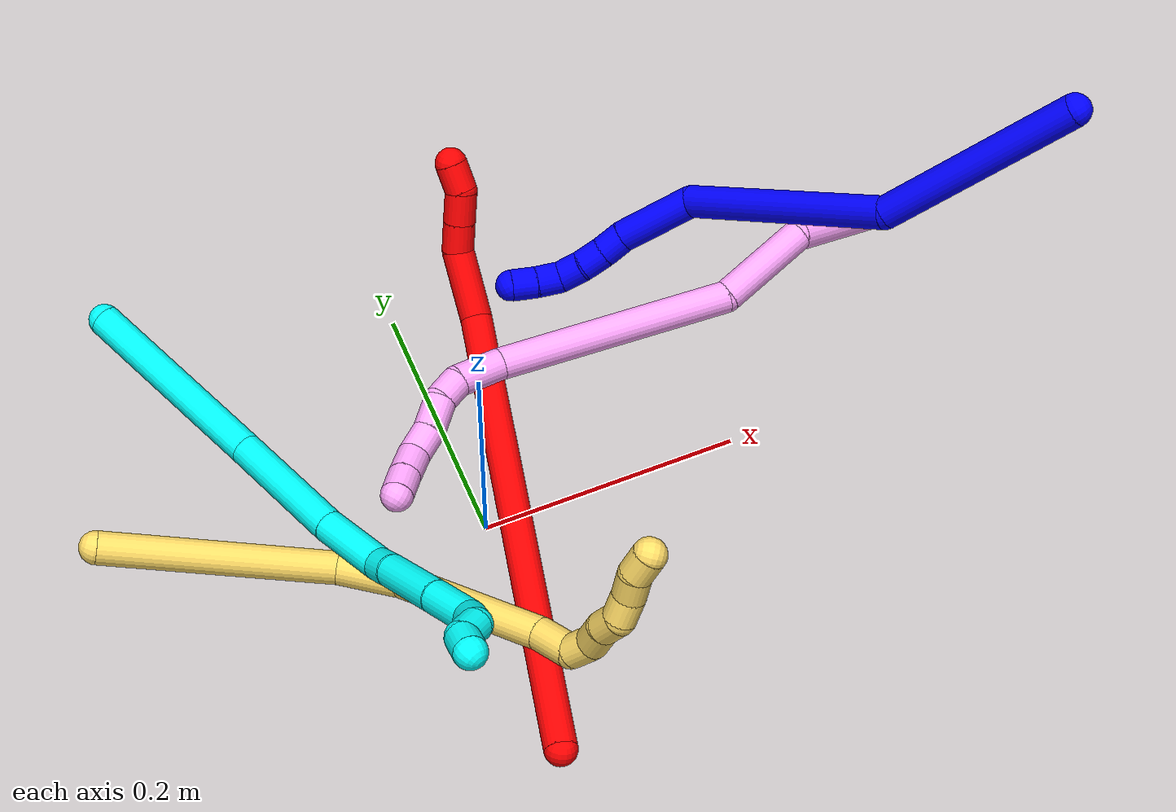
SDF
<sdf version="1.7">
 <world name="default">
  <plugin name="TubeGeneratorPlugin" filename="libtube_generator_plugin.so"/>
  <model name="photoneo_s_sensor">
   <static>1</static>
   <pose>0 0 2 1.57079 1.57079 3.14159</pose>
   <link name="link">
    <inertial><mass>0.1</mass></inertial>
    <sensor name="sensor" type="depth">
     <update_rate>30</update_rate>
     <camera>
      <horizontal_fov>1.22</horizontal_fov>
      <image><width>1920</width><height>1200</height><format>B8G8R8</format></image>
      <clip><near>0.1</near><far>4</far></clip>
      <depth_camera><output>points</output></depth_camera>
     </camera>
     <plugin name="camera_plugin" filename="libgazebo_ros_depth_camera.so">
      <baseline>0.2</baseline>
      <alwaysOn>1</alwaysOn>
      <updateRate>0.0</updateRate>
      <cameraName>camera_ir</cameraName>
      <imageTopicName>/camera/color/image_raw</imageTopicName>
      <cameraInfoTopicName>/camera/color/camera_info</cameraInfoTopicName>
      <depthImageTopicName>/camera/depth/image_raw</depthImageTopicName>
      <depthImageCameraInfoTopicName>/camera/depth/camera_info</depthImageCameraInfoTopicName>
      <pointCloudTopicName>/camera/depth/points</pointCloudTopicName>
      <frameName>fr_optical</frameName>
      <pointCloudCutoff>0.1</pointCloudCutoff>
      <pointCloudCutoffMax>2.0</pointCloudCutoffMax>
      <distortionK1>0</distortionK1>
      <distortionK2>0</distortionK2>
      <distortionK3>0</distortionK3>
      <distortionT1>0</distortionT1>
      <distortionT2>0</distortionT2>
      <CxPrime>0</CxPrime>
      <Cx>0</Cx>
      <Cy>0</Cy>
      <focalLength>0</focalLength>
      <hackBaseline>0</hackBaseline>
     </plugin>
    </sensor>
   </link>
  </model>
  <gravity>0 0 -9.8</gravity>
  <magnetic_field>6e-06 2.3e-05 -4.2e-05</magnetic_field>
  <atmosphere type="adiabatic"/>
  <physics name="default_physics" default="0" type="ode">
   <max_step_size>0.003</max_step_size>
   <real_time_factor>1</real_time_factor>
   <real_time_update_rate>1000</real_time_update_rate>
   <max_contacts>10000</max_contacts>
   <ode>
    <solver>
     <type>quick</type>
     <iters>100</iters>
     <sor>1.3</sor>
     <use_dynamic_moi_rescaling>0</use_dynamic_moi_rescaling>
    </solver>
    <constraints>
     <contact_max_correcting_vel>0</contact_max_correcting_vel>
     <contact_surface_layer>0.001</contact_surface_layer>
     <cfm>0</cfm>
     <erp>0.2</erp>
    </constraints>
   </ode>
  </physics>
  <scene><ambient>0.4 0.4 0.4 1</ambient><background>0.7 0.7 0.7 1</background><shadows>0</shadows></scene>
  <audio><device>default</device></audio>
  <spherical_coordinates>
   <surface_model>EARTH_WGS84</surface_model>
   <latitude_deg>0</latitude_deg>
   <longitude_deg>0</longitude_deg>
   <elevation>0</elevation>
   <heading_deg>0</heading_deg>
  </spherical_coordinates>
  <model name="bin">
   <static>1</static>
   <link name="bottom">
    <collision name="collision-bottom">
     <pose>0 0 -0.01 0 -0 0</pose>
     <geometry><box><size>0.8 0.6 0.02</size></box></geometry>
     <surface>
      <friction><ode><mu>100</mu><mu2>100</mu2></ode></friction>
      <contact><collide_bitmask>65535</collide_bitmask></contact>
     </surface>
    </collision>
   </link>
   <link name="west_wall">
    <collision name="collision-west_wall">
     <pose>-0.41 0 0.1 0 -0 0</pose>
     <geometry><box><size>0.02 0.6 0.2</size></box></geometry>
     <surface>
      <friction><ode><mu>100</mu><mu2>100</mu2></ode></friction>
      <contact><collide_bitmask>65535</collide_bitmask></contact>
     </surface>
    </collision>
   </link>
   <link name="east_wall">
    <collision name="collision-east_wall">
     <pose>0.41 0 0.1 0 -0 0</pose>
     <geometry><box><size>0.02 0.6 0.2</size></box></geometry>
     <surface>
      <friction><ode><mu>100</mu><mu2>100</mu2></ode></friction>
      <contact><collide_bitmask>65535</collide_bitmask></contact>
     </surface>
    </collision>
   </link>
   <link name="south_wall">
    <collision name="collision-south_wall">
     <pose>0 -0.31 0.1 0 -0 0</pose>
     <geometry><box><size>0.8 0.02 0.2</size></box></geometry>
     <surface>
      <friction><ode><mu>100</mu><mu2>100</mu2></ode></friction>
      <contact><collide_bitmask>65535</collide_bitmask></contact>
     </surface>
    </collision>
   </link>
   <link name="north_wall">
    <collision name="collision-north_wall">
     <pose>0 0.31 0.1 0 -0 0</pose>
     <geometry><box><size>0.8 0.02 0.2</size></box></geometry>
     <surface>
      <friction><ode><mu>100</mu><mu2>100</mu2></ode></friction>
      <contact><collide_bitmask>65535</collide_bitmask></contact>
     </surface>
    </collision>
   </link>
  </model>
  <model name="1">
   <static>0</static>
   <link name="1">
    <collision name="collision-cylinder-e_1_1_4">
     <pose>0.025302 0.006108 -0.075731 -3.06112 0.321469 -2.65481</pose>
     <geometry><cylinder><radius>0.0125</radius><length>0.160159</length></cylinder></geometry>
     <surface>
      <friction><ode><mu>1.16</mu><mu2>1.16</mu2><slip1>0</slip1><slip2>0</slip2></ode></friction>
      <contact><ode><kp>1e+06</kp><kd>1</kd><max_vel>0</max_vel><min_depth>0.001</min_depth></ode></contact>
     </surface>
    </collision>
    <visual name="visual-cylinder-e_1_1_4">
     <pose>0.025302 0.006108 -0.075731 -3.06112 0.321469 -2.65481</pose>
     <geometry><cylinder><radius>0.0125</radius><length>0.160159</length></cylinder></geometry>
     <material><ambient>0 0 1 1</ambient></material>
    </visual>
    <collision name="collision-cylinder-e_2_4_5">
     <pose>0.084807 0.061228 -0.216688 -2.49717 0.396961 -1.08445</pose>
     <geometry><cylinder><radius>0.0125</radius><length>0.176934</length></cylinder></geometry>
     <surface>
      <friction><ode><mu>1.16</mu><mu2>1.16</mu2><slip1>0</slip1><slip2>0</slip2></ode></friction>
      <contact><ode><kp>1e+06</kp><kd>1</kd><max_vel>0</max_vel><min_depth>0.001</min_depth></ode></contact>
     </surface>
    </collision>
    <visual name="visual-cylinder-e_2_4_5">
     <pose>0.084807 0.061228 -0.216688 -2.49717 0.396961 -1.08445</pose>
     <geometry><cylinder><radius>0.0125</radius><length>0.176934</length></cylinder></geometry>
     <material><ambient>0 0 1 1</ambient></material>
    </visual>
    <collision name="collision-cylinder-e_3_5_6">
     <pose>0.125028 0.112823 -0.312567 -3.05756 0.193206 -2.32291</pose>
     <geometry><cylinder><radius>0.0125</radius><length>0.062692</length></cylinder></geometry>
     <surface>
      <friction><ode><mu>1.16</mu><mu2>1.16</mu2><slip1>0</slip1><slip2>0</slip2></ode></friction>
      <contact><ode><kp>1e+06</kp><kd>1</kd><max_vel>0</max_vel><min_depth>0.001</min_depth></ode></contact>
     </surface>
    </collision>
    <visual name="visual-cylinder-e_3_5_6">
     <pose>0.125028 0.112823 -0.312567 -3.05756 0.193206 -2.32291</pose>
     <geometry><cylinder><radius>0.0125</radius><length>0.062692</length></cylinder></geometry>
     <material><ambient>0 0 1 1</ambient></material>
    </visual>
    <collision name="collision-cylinder-e_4_6_7">
     <pose>0.131887 0.11392 -0.353153 2.99316 0.08344 1.02314</pose>
     <geometry><cylinder><radius>0.0125</radius><length>0.020154</length></cylinder></geometry>
     <surface>
      <friction><ode><mu>1.16</mu><mu2>1.16</mu2><slip1>0</slip1><slip2>0</slip2></ode></friction>
      <contact><ode><kp>1e+06</kp><kd>1</kd><max_vel>0</max_vel><min_depth>0.001</min_depth></ode></contact>
     </surface>
    </collision>
    <visual name="visual-cylinder-e_4_6_7">
     <pose>0.131887 0.11392 -0.353153 2.99316 0.08344 1.02314</pose>
     <geometry><cylinder><radius>0.0125</radius><length>0.020154</length></cylinder></geometry>
     <material><ambient>0 0 1 1</ambient></material>
    </visual>
    <collision name="collision-cylinder-e_5_7_8">
     <pose>0.132875 0.111631 -0.373066 3.0612 0.014781 0.363483</pose>
     <geometry><cylinder><radius>0.0125</radius><length>0.020031</length></cylinder></geometry>
     <surface>
      <friction><ode><mu>1.16</mu><mu2>1.16</mu2><slip1>0</slip1><slip2>0</slip2></ode></friction>
      <contact><ode><kp>1e+06</kp><kd>1</kd><max_vel>0</max_vel><min_depth>0.001</min_depth></ode></contact>
     </surface>
    </collision>
    <visual name="visual-cylinder-e_5_7_8">
     <pose>0.132875 0.111631 -0.373066 3.0612 0.014781 0.363483</pose>
     <geometry><cylinder><radius>0.0125</radius><length>0.020031</length></cylinder></geometry>
     <material><ambient>0 0 1 1</ambient></material>
    </visual>
    <collision name="collision-cylinder-e_6_8_9">
     <pose>0.134187 0.111385 -0.392973 -3.08535 0.116661 -2.24383</pose>
     <geometry><cylinder><radius>0.0125</radius><length>0.020016</length></cylinder></geometry>
     <surface>
      <friction><ode><mu>1.16</mu><mu2>1.16</mu2><slip1>0</slip1><slip2>0</slip2></ode></friction>
      <contact><ode><kp>1e+06</kp><kd>1</kd><max_vel>0</max_vel><min_depth>0.001</min_depth></ode></contact>
     </surface>
    </collision>
    <visual name="visual-cylinder-e_6_8_9">
     <pose>0.134187 0.111385 -0.392973 -3.08535 0.116661 -2.24383</pose>
     <geometry><cylinder><radius>0.0125</radius><length>0.020016</length></cylinder></geometry>
     <material><ambient>0 0 1 1</ambient></material>
    </visual>
    <collision name="collision-cylinder-e_7_9_10">
     <pose>0.131693 0.113859 -0.412008 -2.93445 -0.374513 2.13808</pose>
     <geometry><cylinder><radius>0.0125</radius><length>0.020008</length></cylinder></geometry>
     <surface>
      <friction><ode><mu>1.16</mu><mu2>1.16</mu2><slip1>0</slip1><slip2>0</slip2></ode></friction>
      <contact><ode><kp>1e+06</kp><kd>1</kd><max_vel>0</max_vel><min_depth>0.001</min_depth></ode></contact>
     </surface>
    </collision>
    <visual name="visual-cylinder-e_7_9_10">
     <pose>0.131693 0.113859 -0.412008 -2.93445 -0.374513 2.13808</pose>
     <geometry><cylinder><radius>0.0125</radius><length>0.020008</length></cylinder></geometry>
     <material><ambient>0 0 1 1</ambient></material>
    </visual>
    <collision name="collision-cylinder-e_8_10_2">
     <pose>0.124373 0.118499 -0.430021 -2.84447 -0.374649 1.80486</pose>
     <geometry><cylinder><radius>0.0125</radius><length>0.020006</length></cylinder></geometry>
     <surface>
      <friction><ode><mu>1.16</mu><mu2>1.16</mu2><slip1>0</slip1><slip2>0</slip2></ode></friction>
      <contact><ode><kp>1e+06</kp><kd>1</kd><max_vel>0</max_vel><min_depth>0.001</min_depth></ode></contact>
     </surface>
    </collision>
    <visual name="visual-cylinder-e_8_10_2">
     <pose>0.124373 0.118499 -0.430021 -2.84447 -0.374649 1.80486</pose>
     <geometry><cylinder><radius>0.0125</radius><length>0.020006</length></cylinder></geometry>
     <material><ambient>0 0 1 1</ambient></material>
    </visual>
    <collision name="collision-sphere-2">
     <pose>0.120712 0.121225 -0.438923 0 -0 0</pose>
     <geometry><sphere><radius>0.0125</radius></sphere></geometry>
     <surface>
      <friction><ode><mu>1.16</mu><mu2>1.16</mu2><slip1>0</slip1><slip2>0</slip2></ode></friction>
      <contact><ode><kp>1e+06</kp><kd>1</kd><max_vel>0</max_vel><min_depth>0.001</min_depth></ode></contact>
     </surface>
    </collision>
    <visual name="visual-sphere-2">
     <pose>0.120712 0.121225 -0.438923 0 -0 0</pose>
     <geometry><sphere><radius>0.0125</radius></sphere></geometry>
     <material><ambient>0 0 1 1</ambient></material>
    </visual>
    <collision name="collision-sphere-10">
     <pose>0.128033 0.115774 -0.42112 0 -0 0</pose>
     <geometry><sphere><radius>0.0125</radius></sphere></geometry>
     <surface>
      <friction><ode><mu>1.16</mu><mu2>1.16</mu2><slip1>0</slip1><slip2>0</slip2></ode></friction>
      <contact><ode><kp>1e+06</kp><kd>1</kd><max_vel>0</max_vel><min_depth>0.001</min_depth></ode></contact>
     </surface>
    </collision>
    <visual name="visual-sphere-10">
     <pose>0.128033 0.115774 -0.42112 0 -0 0</pose>
     <geometry><sphere><radius>0.0125</radius></sphere></geometry>
     <material><ambient>0 0 1 1</ambient></material>
    </visual>
    <collision name="collision-sphere-9">
     <pose>0.135352 0.111944 -0.402897 0 -0 0</pose>
     <geometry><sphere><radius>0.0125</radius></sphere></geometry>
     <surface>
      <friction><ode><mu>1.16</mu><mu2>1.16</mu2><slip1>0</slip1><slip2>0</slip2></ode></friction>
      <contact><ode><kp>1e+06</kp><kd>1</kd><max_vel>0</max_vel><min_depth>0.001</min_depth></ode></contact>
     </surface>
    </collision>
    <visual name="visual-sphere-9">
     <pose>0.135352 0.111944 -0.402897 0 -0 0</pose>
     <geometry><sphere><radius>0.0125</radius></sphere></geometry>
     <material><ambient>0 0 1 1</ambient></material>
    </visual>
    <collision name="collision-sphere-4">
     <pose>0.050604 0.012216 -0.151463 0 -0 0</pose>
     <geometry><sphere><radius>0.0125</radius></sphere></geometry>
     <surface>
      <friction><ode><mu>1.16</mu><mu2>1.16</mu2><slip1>0</slip1><slip2>0</slip2></ode></friction>
      <contact><ode><kp>1e+06</kp><kd>1</kd><max_vel>0</max_vel><min_depth>0.001</min_depth></ode></contact>
     </surface>
    </collision>
    <visual name="visual-sphere-4">
     <pose>0.050604 0.012216 -0.151463 0 -0 0</pose>
     <geometry><sphere><radius>0.0125</radius></sphere></geometry>
     <material><ambient>0 0 1 1</ambient></material>
    </visual>
    <collision name="collision-sphere-1">
     <geometry><sphere><radius>0.0125</radius></sphere></geometry>
     <surface>
      <friction><ode><mu>1.16</mu><mu2>1.16</mu2><slip1>0</slip1><slip2>0</slip2></ode></friction>
      <contact><ode><kp>1e+06</kp><kd>1</kd><max_vel>0</max_vel><min_depth>0.001</min_depth></ode></contact>
     </surface>
    </collision>
    <visual name="visual-sphere-1">
     <geometry><sphere><radius>0.0125</radius></sphere></geometry>
     <material><ambient>0 0 1 1</ambient></material>
    </visual>
    <collision name="collision-sphere-8">
     <pose>0.133023 0.110827 -0.383049 0 -0 0</pose>
     <geometry><sphere><radius>0.0125</radius></sphere></geometry>
     <surface>
      <friction><ode><mu>1.16</mu><mu2>1.16</mu2><slip1>0</slip1><slip2>0</slip2></ode></friction>
      <contact><ode><kp>1e+06</kp><kd>1</kd><max_vel>0</max_vel><min_depth>0.001</min_depth></ode></contact>
     </surface>
    </collision>
    <visual name="visual-sphere-8">
     <pose>0.133023 0.110827 -0.383049 0 -0 0</pose>
     <geometry><sphere><radius>0.0125</radius></sphere></geometry>
     <material><ambient>0 0 1 1</ambient></material>
    </visual>
    <collision name="collision-sphere-5">
     <pose>0.11901 0.110241 -0.281913 0 -0 0</pose>
     <geometry><sphere><radius>0.0125</radius></sphere></geometry>
     <surface>
      <friction><ode><mu>1.16</mu><mu2>1.16</mu2><slip1>0</slip1><slip2>0</slip2></ode></friction>
      <contact><ode><kp>1e+06</kp><kd>1</kd><max_vel>0</max_vel><min_depth>0.001</min_depth></ode></contact>
     </surface>
    </collision>
    <visual name="visual-sphere-5">
     <pose>0.11901 0.110241 -0.281913 0 -0 0</pose>
     <geometry><sphere><radius>0.0125</radius></sphere></geometry>
     <material><ambient>0 0 1 1</ambient></material>
    </visual>
    <collision name="collision-sphere-6">
     <pose>0.131047 0.115405 -0.343221 0 -0 0</pose>
     <geometry><sphere><radius>0.0125</radius></sphere></geometry>
     <surface>
      <friction><ode><mu>1.16</mu><mu2>1.16</mu2><slip1>0</slip1><slip2>0</slip2></ode></friction>
      <contact><ode><kp>1e+06</kp><kd>1</kd><max_vel>0</max_vel><min_depth>0.001</min_depth></ode></contact>
     </surface>
    </collision>
    <visual name="visual-sphere-6">
     <pose>0.131047 0.115405 -0.343221 0 -0 0</pose>
     <geometry><sphere><radius>0.0125</radius></sphere></geometry>
     <material><ambient>0 0 1 1</ambient></material>
    </visual>
    <collision name="collision-sphere-7">
     <pose>0.132726 0.112435 -0.363084 0 -0 0</pose>
     <geometry><sphere><radius>0.0125</radius></sphere></geometry>
     <surface>
      <friction><ode><mu>1.16</mu><mu2>1.16</mu2><slip1>0</slip1><slip2>0</slip2></ode></friction>
      <contact><ode><kp>1e+06</kp><kd>1</kd><max_vel>0</max_vel><min_depth>0.001</min_depth></ode></contact>
     </surface>
    </collision>
    <visual name="visual-sphere-7">
     <pose>0.132726 0.112435 -0.363084 0 -0 0</pose>
     <geometry><sphere><radius>0.0125</radius></sphere></geometry>
     <material><ambient>0 0 1 1</ambient></material>
    </visual>
    <inertial>
     <pose>0.080049 0.06059 -0.218733 0 -0 0</pose>
     <mass>0.5</mass>
     <inertia>
      <ixx>-0.000646</ixx>
      <ixy>0</ixy>
      <ixz>0</ixz>
      <iyy>-0.000292</iyy>
      <iyz>0</iyz>
      <izz>-0.000618</izz>
     </inertia>
    </inertial>
   </link>
   <pose>0.454673 0.013934 0.262805 0.602417 1.05429 0.603729</pose>
  </model>
  <model name="2">
   <static>0</static>
   <link name="2">
    <collision name="collision-cylinder-e_1_1_4">
     <pose>0.013156 0.167827 0.07993 -1.12632 0.070655 -0.04462</pose>
     <geometry><cylinder><radius>0.0125</radius><length>0.372708</length></cylinder></geometry>
     <surface>
      <friction><ode><mu>1.16</mu><mu2>1.16</mu2><slip1>0</slip1><slip2>0</slip2></ode></friction>
      <contact><ode><kp>1e+06</kp><kd>1</kd><max_vel>0</max_vel><min_depth>0.001</min_depth></ode></contact>
     </surface>
    </collision>
    <visual name="visual-cylinder-e_1_1_4">
     <pose>0.013156 0.167827 0.07993 -1.12632 0.070655 -0.04462</pose>
     <geometry><cylinder><radius>0.0125</radius><length>0.372708</length></cylinder></geometry>
     <material><ambient>1 0 0 1</ambient></material>
    </visual>
    <collision name="collision-cylinder-e_2_4_5">
     <pose>0.020377 0.348355 0.183889 -0.486225 -0.215006 0.053519</pose>
     <geometry><cylinder><radius>0.0125</radius><length>0.055638</length></cylinder></geometry>
     <surface>
      <friction><ode><mu>1.16</mu><mu2>1.16</mu2><slip1>0</slip1><slip2>0</slip2></ode></friction>
      <contact><ode><kp>1e+06</kp><kd>1</kd><max_vel>0</max_vel><min_depth>0.001</min_depth></ode></contact>
     </surface>
    </collision>
    <visual name="visual-cylinder-e_2_4_5">
     <pose>0.020377 0.348355 0.183889 -0.486225 -0.215006 0.053519</pose>
     <geometry><cylinder><radius>0.0125</radius><length>0.055638</length></cylinder></geometry>
     <material><ambient>1 0 0 1</ambient></material>
    </visual>
    <collision name="collision-cylinder-e_3_5_6">
     <pose>0.014413 0.36249 0.219748 -0.120754 -0.002356 0.000142</pose>
     <geometry><cylinder><radius>0.0125</radius><length>0.023833</length></cylinder></geometry>
     <surface>
      <friction><ode><mu>1.16</mu><mu2>1.16</mu2><slip1>0</slip1><slip2>0</slip2></ode></friction>
      <contact><ode><kp>1e+06</kp><kd>1</kd><max_vel>0</max_vel><min_depth>0.001</min_depth></ode></contact>
     </surface>
    </collision>
    <visual name="visual-cylinder-e_3_5_6">
     <pose>0.014413 0.36249 0.219748 -0.120754 -0.002356 0.000142</pose>
     <geometry><cylinder><radius>0.0125</radius><length>0.023833</length></cylinder></geometry>
     <material><ambient>1 0 0 1</ambient></material>
    </visual>
    <collision name="collision-cylinder-e_4_6_7">
     <pose>0.014404 0.365305 0.24414 -0.10936 0.001482 -8.1e-05</pose>
     <geometry><cylinder><radius>0.0125</radius><length>0.025276</length></cylinder></geometry>
     <surface>
      <friction><ode><mu>1.16</mu><mu2>1.16</mu2><slip1>0</slip1><slip2>0</slip2></ode></friction>
      <contact><ode><kp>1e+06</kp><kd>1</kd><max_vel>0</max_vel><min_depth>0.001</min_depth></ode></contact>
     </surface>
    </collision>
    <visual name="visual-cylinder-e_4_6_7">
     <pose>0.014404 0.365305 0.24414 -0.10936 0.001482 -8.1e-05</pose>
     <geometry><cylinder><radius>0.0125</radius><length>0.025276</length></cylinder></geometry>
     <material><ambient>1 0 0 1</ambient></material>
    </visual>
    <collision name="collision-cylinder-e_5_7_2">
     <pose>0.010605 0.370601 0.266558 -0.378264 -0.345557 0.066788</pose>
     <geometry><cylinder><radius>0.0125</radius><length>0.022544</length></cylinder></geometry>
     <surface>
      <friction><ode><mu>1.16</mu><mu2>1.16</mu2><slip1>0</slip1><slip2>0</slip2></ode></friction>
      <contact><ode><kp>1e+06</kp><kd>1</kd><max_vel>0</max_vel><min_depth>0.001</min_depth></ode></contact>
     </surface>
    </collision>
    <visual name="visual-cylinder-e_5_7_2">
     <pose>0.010605 0.370601 0.266558 -0.378264 -0.345557 0.066788</pose>
     <geometry><cylinder><radius>0.0125</radius><length>0.022544</length></cylinder></geometry>
     <material><ambient>1 0 0 1</ambient></material>
    </visual>
    <collision name="collision-sphere-2">
     <pose>0.006786 0.374518 0.276414 0 -0 0</pose>
     <geometry><sphere><radius>0.0125</radius></sphere></geometry>
     <surface>
      <friction><ode><mu>1.16</mu><mu2>1.16</mu2><slip1>0</slip1><slip2>0</slip2></ode></friction>
      <contact><ode><kp>1e+06</kp><kd>1</kd><max_vel>0</max_vel><min_depth>0.001</min_depth></ode></contact>
     </surface>
    </collision>
    <visual name="visual-sphere-2">
     <pose>0.006786 0.374518 0.276414 0 -0 0</pose>
     <geometry><sphere><radius>0.0125</radius></sphere></geometry>
     <material><ambient>1 0 0 1</ambient></material>
    </visual>
    <collision name="collision-sphere-7">
     <pose>0.014423 0.366685 0.256702 0 -0 0</pose>
     <geometry><sphere><radius>0.0125</radius></sphere></geometry>
     <surface>
      <friction><ode><mu>1.16</mu><mu2>1.16</mu2><slip1>0</slip1><slip2>0</slip2></ode></friction>
      <contact><ode><kp>1e+06</kp><kd>1</kd><max_vel>0</max_vel><min_depth>0.001</min_depth></ode></contact>
     </surface>
    </collision>
    <visual name="visual-sphere-7">
     <pose>0.014423 0.366685 0.256702 0 -0 0</pose>
     <geometry><sphere><radius>0.0125</radius></sphere></geometry>
     <material><ambient>1 0 0 1</ambient></material>
    </visual>
    <collision name="collision-sphere-6">
     <pose>0.014385 0.363926 0.231577 0 -0 0</pose>
     <geometry><sphere><radius>0.0125</radius></sphere></geometry>
     <surface>
      <friction><ode><mu>1.16</mu><mu2>1.16</mu2><slip1>0</slip1><slip2>0</slip2></ode></friction>
      <contact><ode><kp>1e+06</kp><kd>1</kd><max_vel>0</max_vel><min_depth>0.001</min_depth></ode></contact>
     </surface>
    </collision>
    <visual name="visual-sphere-6">
     <pose>0.014385 0.363926 0.231577 0 -0 0</pose>
     <geometry><sphere><radius>0.0125</radius></sphere></geometry>
     <material><ambient>1 0 0 1</ambient></material>
    </visual>
    <collision name="collision-sphere-5">
     <pose>0.014441 0.361055 0.207918 0 -0 0</pose>
     <geometry><sphere><radius>0.0125</radius></sphere></geometry>
     <surface>
      <friction><ode><mu>1.16</mu><mu2>1.16</mu2><slip1>0</slip1><slip2>0</slip2></ode></friction>
      <contact><ode><kp>1e+06</kp><kd>1</kd><max_vel>0</max_vel><min_depth>0.001</min_depth></ode></contact>
     </surface>
    </collision>
    <visual name="visual-sphere-5">
     <pose>0.014441 0.361055 0.207918 0 -0 0</pose>
     <geometry><sphere><radius>0.0125</radius></sphere></geometry>
     <material><ambient>1 0 0 1</ambient></material>
    </visual>
    <collision name="collision-sphere-1">
     <geometry><sphere><radius>0.0125</radius></sphere></geometry>
     <surface>
      <friction><ode><mu>1.16</mu><mu2>1.16</mu2><slip1>0</slip1><slip2>0</slip2></ode></friction>
      <contact><ode><kp>1e+06</kp><kd>1</kd><max_vel>0</max_vel><min_depth>0.001</min_depth></ode></contact>
     </surface>
    </collision>
    <visual name="visual-sphere-1">
     <geometry><sphere><radius>0.0125</radius></sphere></geometry>
     <material><ambient>1 0 0 1</ambient></material>
    </visual>
    <collision name="collision-sphere-4">
     <pose>0.026312 0.335654 0.159861 0 -0 0</pose>
     <geometry><sphere><radius>0.0125</radius></sphere></geometry>
     <surface>
      <friction><ode><mu>1.16</mu><mu2>1.16</mu2><slip1>0</slip1><slip2>0</slip2></ode></friction>
      <contact><ode><kp>1e+06</kp><kd>1</kd><max_vel>0</max_vel><min_depth>0.001</min_depth></ode></contact>
     </surface>
    </collision>
    <visual name="visual-sphere-4">
     <pose>0.026312 0.335654 0.159861 0 -0 0</pose>
     <geometry><sphere><radius>0.0125</radius></sphere></geometry>
     <material><ambient>1 0 0 1</ambient></material>
    </visual>
    <inertial>
     <pose>0.013967 0.21632 0.114879 0 -0 0</pose>
     <mass>0.5</mass>
     <inertia>
      <ixx>0.004145</ixx>
      <ixy>0</ixy>
      <ixz>0</ixz>
      <iyy>0.00173</iyy>
      <iyz>0</iyz>
      <izz>-0.004187</izz>
     </inertia>
    </inertial>
   </link>
   <pose>-0.019035 -0.1926 0.011499 -0.427066 0.24132 -0.139647</pose>
  </model>
  <model name="3">
   <static>0</static>
   <link name="3">
    <collision name="collision-cylinder-e_1_1_4">
     <pose>0.000249 0.009169 -0.079318 -3.0265 0.003118 -0.054104</pose>
     <geometry><cylinder><radius>0.0125</radius><length>0.159693</length></cylinder></geometry>
     <surface>
      <friction><ode><mu>1.16</mu><mu2>1.16</mu2><slip1>0</slip1><slip2>0</slip2></ode></friction>
      <contact><ode><kp>1e+06</kp><kd>1</kd><max_vel>0</max_vel><min_depth>0.001</min_depth></ode></contact>
     </surface>
    </collision>
    <visual name="visual-cylinder-e_1_1_4">
     <pose>0.000249 0.009169 -0.079318 -3.0265 0.003118 -0.054104</pose>
     <geometry><cylinder><radius>0.0125</radius><length>0.159693</length></cylinder></geometry>
     <material><ambient>0.003922 1 0.996078 1</ambient></material>
    </visual>
    <collision name="collision-cylinder-e_2_4_5">
     <pose>0.012031 0.016451 -0.209741 3.10468 0.221813 2.8131</pose>
     <geometry><cylinder><radius>0.0125</radius><length>0.104848</length></cylinder></geometry>
     <surface>
      <friction><ode><mu>1.16</mu><mu2>1.16</mu2><slip1>0</slip1><slip2>0</slip2></ode></friction>
      <contact><ode><kp>1e+06</kp><kd>1</kd><max_vel>0</max_vel><min_depth>0.001</min_depth></ode></contact>
     </surface>
    </collision>
    <visual name="visual-cylinder-e_2_4_5">
     <pose>0.012031 0.016451 -0.209741 3.10468 0.221813 2.8131</pose>
     <geometry><cylinder><radius>0.0125</radius><length>0.104848</length></cylinder></geometry>
     <material><ambient>0.003922 1 0.996078 1</ambient></material>
    </visual>
    <collision name="collision-cylinder-e_3_5_6">
     <pose>0.031515 0.015057 -0.287845 -3.12335 0.286342 -3.01518</pose>
     <geometry><cylinder><radius>0.0125</radius><length>0.056301</length></cylinder></geometry>
     <surface>
      <friction><ode><mu>1.16</mu><mu2>1.16</mu2><slip1>0</slip1><slip2>0</slip2></ode></friction>
      <contact><ode><kp>1e+06</kp><kd>1</kd><max_vel>0</max_vel><min_depth>0.001</min_depth></ode></contact>
     </surface>
    </collision>
    <visual name="visual-cylinder-e_3_5_6">
     <pose>0.031515 0.015057 -0.287845 -3.12335 0.286342 -3.01518</pose>
     <geometry><cylinder><radius>0.0125</radius><length>0.056301</length></cylinder></geometry>
     <material><ambient>0.003922 1 0.996078 1</ambient></material>
    </visual>
    <collision name="collision-cylinder-e_4_6_7">
     <pose>0.046554 0.013446 -0.322991 2.88891 0.700115 2.47197</pose>
     <geometry><cylinder><radius>0.0125</radius><length>0.022003</length></cylinder></geometry>
     <surface>
      <friction><ode><mu>1.16</mu><mu2>1.16</mu2><slip1>0</slip1><slip2>0</slip2></ode></friction>
      <contact><ode><kp>1e+06</kp><kd>1</kd><max_vel>0</max_vel><min_depth>0.001</min_depth></ode></contact>
     </surface>
    </collision>
    <visual name="visual-cylinder-e_4_6_7">
     <pose>0.046554 0.013446 -0.322991 2.88891 0.700115 2.47197</pose>
     <geometry><cylinder><radius>0.0125</radius><length>0.022003</length></cylinder></geometry>
     <material><ambient>0.003922 1 0.996078 1</ambient></material>
    </visual>
    <collision name="collision-cylinder-e_5_7_8">
     <pose>0.069086 0.008302 -0.355095 3.01534 0.568948 2.7158</pose>
     <geometry><cylinder><radius>0.0125</radius><length>0.057331</length></cylinder></geometry>
     <surface>
      <friction><ode><mu>1.16</mu><mu2>1.16</mu2><slip1>0</slip1><slip2>0</slip2></ode></friction>
      <contact><ode><kp>1e+06</kp><kd>1</kd><max_vel>0</max_vel><min_depth>0.001</min_depth></ode></contact>
     </surface>
    </collision>
    <visual name="visual-cylinder-e_5_7_8">
     <pose>0.069086 0.008302 -0.355095 3.01534 0.568948 2.7158</pose>
     <geometry><cylinder><radius>0.0125</radius><length>0.057331</length></cylinder></geometry>
     <material><ambient>0.003922 1 0.996078 1</ambient></material>
    </visual>
    <collision name="collision-cylinder-e_6_8_9">
     <pose>0.093943 0.004219 -0.396174 3.08082 0.501915 2.90557</pose>
     <geometry><cylinder><radius>0.0125</radius><length>0.039132</length></cylinder></geometry>
     <surface>
      <friction><ode><mu>1.16</mu><mu2>1.16</mu2><slip1>0</slip1><slip2>0</slip2></ode></friction>
      <contact><ode><kp>1e+06</kp><kd>1</kd><max_vel>0</max_vel><min_depth>0.001</min_depth></ode></contact>
     </surface>
    </collision>
    <visual name="visual-cylinder-e_6_8_9">
     <pose>0.093943 0.004219 -0.396174 3.08082 0.501915 2.90557</pose>
     <geometry><cylinder><radius>0.0125</radius><length>0.039132</length></cylinder></geometry>
     <material><ambient>0.003922 1 0.996078 1</ambient></material>
    </visual>
    <collision name="collision-cylinder-e_7_9_10">
     <pose>0.109996 -0.001171 -0.419538 2.53317 0.717575 1.74759</pose>
     <geometry><cylinder><radius>0.0125</radius><length>0.020196</length></cylinder></geometry>
     <surface>
      <friction><ode><mu>1.16</mu><mu2>1.16</mu2><slip1>0</slip1><slip2>0</slip2></ode></friction>
      <contact><ode><kp>1e+06</kp><kd>1</kd><max_vel>0</max_vel><min_depth>0.001</min_depth></ode></contact>
     </surface>
    </collision>
    <visual name="visual-cylinder-e_7_9_10">
     <pose>0.109996 -0.001171 -0.419538 2.53317 0.717575 1.74759</pose>
     <geometry><cylinder><radius>0.0125</radius><length>0.020196</length></cylinder></geometry>
     <material><ambient>0.003922 1 0.996078 1</ambient></material>
    </visual>
    <collision name="collision-cylinder-e_8_10_11">
     <pose>0.119908 -0.014782 -0.428681 1.87429 0.325137 0.439267</pose>
     <geometry><cylinder><radius>0.0125</radius><length>0.020485</length></cylinder></geometry>
     <surface>
      <friction><ode><mu>1.16</mu><mu2>1.16</mu2><slip1>0</slip1><slip2>0</slip2></ode></friction>
      <contact><ode><kp>1e+06</kp><kd>1</kd><max_vel>0</max_vel><min_depth>0.001</min_depth></ode></contact>
     </surface>
    </collision>
    <visual name="visual-cylinder-e_8_10_11">
     <pose>0.119908 -0.014782 -0.428681 1.87429 0.325137 0.439267</pose>
     <geometry><cylinder><radius>0.0125</radius><length>0.020485</length></cylinder></geometry>
     <material><ambient>0.003922 1 0.996078 1</ambient></material>
    </visual>
    <collision name="collision-cylinder-e_9_11_2">
     <pose>0.127664 -0.028196 -0.439504 2.65885 0.464716 1.53129</pose>
     <geometry><cylinder><radius>0.0125</radius><length>0.020011</length></cylinder></geometry>
     <surface>
      <friction><ode><mu>1.16</mu><mu2>1.16</mu2><slip1>0</slip1><slip2>0</slip2></ode></friction>
      <contact><ode><kp>1e+06</kp><kd>1</kd><max_vel>0</max_vel><min_depth>0.001</min_depth></ode></contact>
     </surface>
    </collision>
    <visual name="visual-cylinder-e_9_11_2">
     <pose>0.127664 -0.028196 -0.439504 2.65885 0.464716 1.53129</pose>
     <geometry><cylinder><radius>0.0125</radius><length>0.020011</length></cylinder></geometry>
     <material><ambient>0.003922 1 0.996078 1</ambient></material>
    </visual>
    <collision name="collision-sphere-2">
     <pose>0.132148 -0.032348 -0.447426 0 -0 0</pose>
     <geometry><sphere><radius>0.0125</radius></sphere></geometry>
     <surface>
      <friction><ode><mu>1.16</mu><mu2>1.16</mu2><slip1>0</slip1><slip2>0</slip2></ode></friction>
      <contact><ode><kp>1e+06</kp><kd>1</kd><max_vel>0</max_vel><min_depth>0.001</min_depth></ode></contact>
     </surface>
    </collision>
    <visual name="visual-sphere-2">
     <pose>0.132148 -0.032348 -0.447426 0 -0 0</pose>
     <geometry><sphere><radius>0.0125</radius></sphere></geometry>
     <material><ambient>0.003922 1 0.996078 1</ambient></material>
    </visual>
    <collision name="collision-sphere-11">
     <pose>0.12318 -0.024044 -0.431581 0 -0 0</pose>
     <geometry><sphere><radius>0.0125</radius></sphere></geometry>
     <surface>
      <friction><ode><mu>1.16</mu><mu2>1.16</mu2><slip1>0</slip1><slip2>0</slip2></ode></friction>
      <contact><ode><kp>1e+06</kp><kd>1</kd><max_vel>0</max_vel><min_depth>0.001</min_depth></ode></contact>
     </surface>
    </collision>
    <visual name="visual-sphere-11">
     <pose>0.12318 -0.024044 -0.431581 0 -0 0</pose>
     <geometry><sphere><radius>0.0125</radius></sphere></geometry>
     <material><ambient>0.003922 1 0.996078 1</ambient></material>
    </visual>
    <collision name="collision-sphere-10">
     <pose>0.116636 -0.005519 -0.42578 0 -0 0</pose>
     <geometry><sphere><radius>0.0125</radius></sphere></geometry>
     <surface>
      <friction><ode><mu>1.16</mu><mu2>1.16</mu2><slip1>0</slip1><slip2>0</slip2></ode></friction>
      <contact><ode><kp>1e+06</kp><kd>1</kd><max_vel>0</max_vel><min_depth>0.001</min_depth></ode></contact>
     </surface>
    </collision>
    <visual name="visual-sphere-10">
     <pose>0.116636 -0.005519 -0.42578 0 -0 0</pose>
     <geometry><sphere><radius>0.0125</radius></sphere></geometry>
     <material><ambient>0.003922 1 0.996078 1</ambient></material>
    </visual>
    <collision name="collision-sphere-9">
     <pose>0.103356 0.003178 -0.413295 0 -0 0</pose>
     <geometry><sphere><radius>0.0125</radius></sphere></geometry>
     <surface>
      <friction><ode><mu>1.16</mu><mu2>1.16</mu2><slip1>0</slip1><slip2>0</slip2></ode></friction>
      <contact><ode><kp>1e+06</kp><kd>1</kd><max_vel>0</max_vel><min_depth>0.001</min_depth></ode></contact>
     </surface>
    </collision>
    <visual name="visual-sphere-9">
     <pose>0.103356 0.003178 -0.413295 0 -0 0</pose>
     <geometry><sphere><radius>0.0125</radius></sphere></geometry>
     <material><ambient>0.003922 1 0.996078 1</ambient></material>
    </visual>
    <collision name="collision-sphere-4">
     <pose>0.000498 0.018339 -0.158636 0 -0 0</pose>
     <geometry><sphere><radius>0.0125</radius></sphere></geometry>
     <surface>
      <friction><ode><mu>1.16</mu><mu2>1.16</mu2><slip1>0</slip1><slip2>0</slip2></ode></friction>
      <contact><ode><kp>1e+06</kp><kd>1</kd><max_vel>0</max_vel><min_depth>0.001</min_depth></ode></contact>
     </surface>
    </collision>
    <visual name="visual-sphere-4">
     <pose>0.000498 0.018339 -0.158636 0 -0 0</pose>
     <geometry><sphere><radius>0.0125</radius></sphere></geometry>
     <material><ambient>0.003922 1 0.996078 1</ambient></material>
    </visual>
    <collision name="collision-sphere-1">
     <geometry><sphere><radius>0.0125</radius></sphere></geometry>
     <surface>
      <friction><ode><mu>1.16</mu><mu2>1.16</mu2><slip1>0</slip1><slip2>0</slip2></ode></friction>
      <contact><ode><kp>1e+06</kp><kd>1</kd><max_vel>0</max_vel><min_depth>0.001</min_depth></ode></contact>
     </surface>
    </collision>
    <visual name="visual-sphere-1">
     <geometry><sphere><radius>0.0125</radius></sphere></geometry>
     <material><ambient>0.003922 1 0.996078 1</ambient></material>
    </visual>
    <collision name="collision-sphere-8">
     <pose>0.08453 0.005261 -0.379053 0 -0 0</pose>
     <geometry><sphere><radius>0.0125</radius></sphere></geometry>
     <surface>
      <friction><ode><mu>1.16</mu><mu2>1.16</mu2><slip1>0</slip1><slip2>0</slip2></ode></friction>
      <contact><ode><kp>1e+06</kp><kd>1</kd><max_vel>0</max_vel><min_depth>0.001</min_depth></ode></contact>
     </surface>
    </collision>
    <visual name="visual-sphere-8">
     <pose>0.08453 0.005261 -0.379053 0 -0 0</pose>
     <geometry><sphere><radius>0.0125</radius></sphere></geometry>
     <material><ambient>0.003922 1 0.996078 1</ambient></material>
    </visual>
    <collision name="collision-sphere-5">
     <pose>0.023564 0.014564 -0.260845 0 -0 0</pose>
     <geometry><sphere><radius>0.0125</radius></sphere></geometry>
     <surface>
      <friction><ode><mu>1.16</mu><mu2>1.16</mu2><slip1>0</slip1><slip2>0</slip2></ode></friction>
      <contact><ode><kp>1e+06</kp><kd>1</kd><max_vel>0</max_vel><min_depth>0.001</min_depth></ode></contact>
     </surface>
    </collision>
    <visual name="visual-sphere-5">
     <pose>0.023564 0.014564 -0.260845 0 -0 0</pose>
     <geometry><sphere><radius>0.0125</radius></sphere></geometry>
     <material><ambient>0.003922 1 0.996078 1</ambient></material>
    </visual>
    <collision name="collision-sphere-6">
     <pose>0.039466 0.01555 -0.314845 0 -0 0</pose>
     <geometry><sphere><radius>0.0125</radius></sphere></geometry>
     <surface>
      <friction><ode><mu>1.16</mu><mu2>1.16</mu2><slip1>0</slip1><slip2>0</slip2></ode></friction>
      <contact><ode><kp>1e+06</kp><kd>1</kd><max_vel>0</max_vel><min_depth>0.001</min_depth></ode></contact>
     </surface>
    </collision>
    <visual name="visual-sphere-6">
     <pose>0.039466 0.01555 -0.314845 0 -0 0</pose>
     <geometry><sphere><radius>0.0125</radius></sphere></geometry>
     <material><ambient>0.003922 1 0.996078 1</ambient></material>
    </visual>
    <collision name="collision-sphere-7">
     <pose>0.053643 0.011343 -0.331138 0 -0 0</pose>
     <geometry><sphere><radius>0.0125</radius></sphere></geometry>
     <surface>
      <friction><ode><mu>1.16</mu><mu2>1.16</mu2><slip1>0</slip1><slip2>0</slip2></ode></friction>
      <contact><ode><kp>1e+06</kp><kd>1</kd><max_vel>0</max_vel><min_depth>0.001</min_depth></ode></contact>
     </surface>
    </collision>
    <visual name="visual-sphere-7">
     <pose>0.053643 0.011343 -0.331138 0 -0 0</pose>
     <geometry><sphere><radius>0.0125</radius></sphere></geometry>
     <material><ambient>0.003922 1 0.996078 1</ambient></material>
    </visual>
    <inertial>
     <pose>0.037939 0.008166 -0.239761 0 -0 0</pose>
     <mass>0.5</mass>
     <inertia>
      <ixx>0.00025</ixx>
      <ixy>0</ixy>
      <ixz>0</ixz>
      <iyy>-0.000186</iyy>
      <iyz>0</iyz>
      <izz>-0.00011</izz>
     </inertia>
    </inertial>
   </link>
   <pose>-0.20976 0.27201 0.024868 -1.39141 -1.30467 0.132995</pose>
  </model>
  <model name="4">
   <static>0</static>
   <link name="4">
    <collision name="collision-cylinder-e_1_1_4">
     <pose>-0.027607 -0.014427 -0.026192 2.63813 -0.745514 -1.97805</pose>
     <geometry><cylinder><radius>0.0125</radius><length>0.081395</length></cylinder></geometry>
     <surface>
      <friction><ode><mu>1.16</mu><mu2>1.16</mu2><slip1>0</slip1><slip2>0</slip2></ode></friction>
      <contact><ode><kp>1e+06</kp><kd>1</kd><max_vel>0</max_vel><min_depth>0.001</min_depth></ode></contact>
     </surface>
    </collision>
    <visual name="visual-cylinder-e_1_1_4">
     <pose>-0.027607 -0.014427 -0.026192 2.63813 -0.745514 -1.97805</pose>
     <geometry><cylinder><radius>0.0125</radius><length>0.081395</length></cylinder></geometry>
     <material><ambient>1 0.65098 0.996078 1</ambient></material>
    </visual>
    <collision name="collision-cylinder-e_2_4_5">
     <pose>-0.069598 -0.031298 -0.088831 3.07461 -0.37512 -2.79211</pose>
     <geometry><cylinder><radius>0.0125</radius><length>0.078518</length></cylinder></geometry>
     <surface>
      <friction><ode><mu>1.16</mu><mu2>1.16</mu2><slip1>0</slip1><slip2>0</slip2></ode></friction>
      <contact><ode><kp>1e+06</kp><kd>1</kd><max_vel>0</max_vel><min_depth>0.001</min_depth></ode></contact>
     </surface>
    </collision>
    <visual name="visual-cylinder-e_2_4_5">
     <pose>-0.069598 -0.031298 -0.088831 3.07461 -0.37512 -2.79211</pose>
     <geometry><cylinder><radius>0.0125</radius><length>0.078518</length></cylinder></geometry>
     <material><ambient>1 0.65098 0.996078 1</ambient></material>
    </visual>
    <collision name="collision-cylinder-e_3_5_6">
     <pose>-0.146716 -0.022503 -0.192156 -2.97507 -0.746487 2.72166</pose>
     <geometry><cylinder><radius>0.0125</radius><length>0.184765</length></cylinder></geometry>
     <surface>
      <friction><ode><mu>1.16</mu><mu2>1.16</mu2><slip1>0</slip1><slip2>0</slip2></ode></friction>
      <contact><ode><kp>1e+06</kp><kd>1</kd><max_vel>0</max_vel><min_depth>0.001</min_depth></ode></contact>
     </surface>
    </collision>
    <visual name="visual-cylinder-e_3_5_6">
     <pose>-0.146716 -0.022503 -0.192156 -2.97507 -0.746487 2.72166</pose>
     <geometry><cylinder><radius>0.0125</radius><length>0.184765</length></cylinder></geometry>
     <material><ambient>1 0.65098 0.996078 1</ambient></material>
    </visual>
    <collision name="collision-cylinder-e_4_6_7">
     <pose>-0.221814 -0.014716 -0.273547 2.90797 -0.692034 -2.51224</pose>
     <geometry><cylinder><radius>0.0125</radius><length>0.038753</length></cylinder></geometry>
     <surface>
      <friction><ode><mu>1.16</mu><mu2>1.16</mu2><slip1>0</slip1><slip2>0</slip2></ode></friction>
      <contact><ode><kp>1e+06</kp><kd>1</kd><max_vel>0</max_vel><min_depth>0.001</min_depth></ode></contact>
     </surface>
    </collision>
    <visual name="visual-cylinder-e_4_6_7">
     <pose>-0.221814 -0.014716 -0.273547 2.90797 -0.692034 -2.51224</pose>
     <geometry><cylinder><radius>0.0125</radius><length>0.038753</length></cylinder></geometry>
     <material><ambient>1 0.65098 0.996078 1</ambient></material>
    </visual>
    <collision name="collision-cylinder-e_5_7_8">
     <pose>-0.23731 -0.021752 -0.29787 2.79143 -0.291424 -1.38508</pose>
     <geometry><cylinder><radius>0.0125</radius><length>0.021806</length></cylinder></geometry>
     <surface>
      <friction><ode><mu>1.16</mu><mu2>1.16</mu2><slip1>0</slip1><slip2>0</slip2></ode></friction>
      <contact><ode><kp>1e+06</kp><kd>1</kd><max_vel>0</max_vel><min_depth>0.001</min_depth></ode></contact>
     </surface>
    </collision>
    <visual name="visual-cylinder-e_5_7_8">
     <pose>-0.23731 -0.021752 -0.29787 2.79143 -0.291424 -1.38508</pose>
     <geometry><cylinder><radius>0.0125</radius><length>0.021806</length></cylinder></geometry>
     <material><ambient>1 0.65098 0.996078 1</ambient></material>
    </visual>
    <collision name="collision-cylinder-e_6_8_9">
     <pose>-0.23947 -0.029472 -0.320086 2.81973 0.074247 0.449835</pose>
     <geometry><cylinder><radius>0.0125</radius><length>0.026227</length></cylinder></geometry>
     <surface>
      <friction><ode><mu>1.16</mu><mu2>1.16</mu2><slip1>0</slip1><slip2>0</slip2></ode></friction>
      <contact><ode><kp>1e+06</kp><kd>1</kd><max_vel>0</max_vel><min_depth>0.001</min_depth></ode></contact>
     </surface>
    </collision>
    <visual name="visual-cylinder-e_6_8_9">
     <pose>-0.23947 -0.029472 -0.320086 2.81973 0.074247 0.449835</pose>
     <geometry><cylinder><radius>0.0125</radius><length>0.026227</length></cylinder></geometry>
     <material><ambient>1 0.65098 0.996078 1</ambient></material>
    </visual>
    <collision name="collision-cylinder-e_7_9_10">
     <pose>-0.239755 -0.036229 -0.343083 2.89909 -0.114717 -0.880764</pose>
     <geometry><cylinder><radius>0.0125</radius><length>0.021966</length></cylinder></geometry>
     <surface>
      <friction><ode><mu>1.16</mu><mu2>1.16</mu2><slip1>0</slip1><slip2>0</slip2></ode></friction>
      <contact><ode><kp>1e+06</kp><kd>1</kd><max_vel>0</max_vel><min_depth>0.001</min_depth></ode></contact>
     </surface>
    </collision>
    <visual name="visual-cylinder-e_7_9_10">
     <pose>-0.239755 -0.036229 -0.343083 2.89909 -0.114717 -0.880764</pose>
     <geometry><cylinder><radius>0.0125</radius><length>0.021966</length></cylinder></geometry>
     <material><ambient>1 0.65098 0.996078 1</ambient></material>
    </visual>
    <collision name="collision-cylinder-e_8_10_11">
     <pose>-0.242512 -0.047199 -0.362835 2.40245 -0.120394 -0.3087</pose>
     <geometry><cylinder><radius>0.0125</radius><length>0.024972</length></cylinder></geometry>
     <surface>
      <friction><ode><mu>1.16</mu><mu2>1.16</mu2><slip1>0</slip1><slip2>0</slip2></ode></friction>
      <contact><ode><kp>1e+06</kp><kd>1</kd><max_vel>0</max_vel><min_depth>0.001</min_depth></ode></contact>
     </surface>
    </collision>
    <visual name="visual-cylinder-e_8_10_11">
     <pose>-0.242512 -0.047199 -0.362835 2.40245 -0.120394 -0.3087</pose>
     <geometry><cylinder><radius>0.0125</radius><length>0.024972</length></cylinder></geometry>
     <material><ambient>1 0.65098 0.996078 1</ambient></material>
    </visual>
    <collision name="collision-cylinder-e_9_11_2">
     <pose>-0.244924 -0.062926 -0.379831 2.38628 -0.084648 -0.212704</pose>
     <geometry><cylinder><radius>0.0125</radius><length>0.021598</length></cylinder></geometry>
     <surface>
      <friction><ode><mu>1.16</mu><mu2>1.16</mu2><slip1>0</slip1><slip2>0</slip2></ode></friction>
      <contact><ode><kp>1e+06</kp><kd>1</kd><max_vel>0</max_vel><min_depth>0.001</min_depth></ode></contact>
     </surface>
    </collision>
    <visual name="visual-cylinder-e_9_11_2">
     <pose>-0.244924 -0.062926 -0.379831 2.38628 -0.084648 -0.212704</pose>
     <geometry><cylinder><radius>0.0125</radius><length>0.021598</length></cylinder></geometry>
     <material><ambient>1 0.65098 0.996078 1</ambient></material>
    </visual>
    <collision name="collision-sphere-2">
     <pose>-0.245837 -0.070303 -0.387665 0 -0 0</pose>
     <geometry><sphere><radius>0.0125</radius></sphere></geometry>
     <surface>
      <friction><ode><mu>1.16</mu><mu2>1.16</mu2><slip1>0</slip1><slip2>0</slip2></ode></friction>
      <contact><ode><kp>1e+06</kp><kd>1</kd><max_vel>0</max_vel><min_depth>0.001</min_depth></ode></contact>
     </surface>
    </collision>
    <visual name="visual-sphere-2">
     <pose>-0.245837 -0.070303 -0.387665 0 -0 0</pose>
     <geometry><sphere><radius>0.0125</radius></sphere></geometry>
     <material><ambient>1 0.65098 0.996078 1</ambient></material>
    </visual>
    <collision name="collision-sphere-11">
     <pose>-0.244011 -0.05555 -0.371996 0 -0 0</pose>
     <geometry><sphere><radius>0.0125</radius></sphere></geometry>
     <surface>
      <friction><ode><mu>1.16</mu><mu2>1.16</mu2><slip1>0</slip1><slip2>0</slip2></ode></friction>
      <contact><ode><kp>1e+06</kp><kd>1</kd><max_vel>0</max_vel><min_depth>0.001</min_depth></ode></contact>
     </surface>
    </collision>
    <visual name="visual-sphere-11">
     <pose>-0.244011 -0.05555 -0.371996 0 -0 0</pose>
     <geometry><sphere><radius>0.0125</radius></sphere></geometry>
     <material><ambient>1 0.65098 0.996078 1</ambient></material>
    </visual>
    <collision name="collision-sphere-10">
     <pose>-0.241012 -0.038849 -0.353674 0 -0 0</pose>
     <geometry><sphere><radius>0.0125</radius></sphere></geometry>
     <surface>
      <friction><ode><mu>1.16</mu><mu2>1.16</mu2><slip1>0</slip1><slip2>0</slip2></ode></friction>
      <contact><ode><kp>1e+06</kp><kd>1</kd><max_vel>0</max_vel><min_depth>0.001</min_depth></ode></contact>
     </surface>
    </collision>
    <visual name="visual-sphere-10">
     <pose>-0.241012 -0.038849 -0.353674 0 -0 0</pose>
     <geometry><sphere><radius>0.0125</radius></sphere></geometry>
     <material><ambient>1 0.65098 0.996078 1</ambient></material>
    </visual>
    <collision name="collision-sphere-9">
     <pose>-0.238498 -0.033609 -0.332491 0 -0 0</pose>
     <geometry><sphere><radius>0.0125</radius></sphere></geometry>
     <surface>
      <friction><ode><mu>1.16</mu><mu2>1.16</mu2><slip1>0</slip1><slip2>0</slip2></ode></friction>
      <contact><ode><kp>1e+06</kp><kd>1</kd><max_vel>0</max_vel><min_depth>0.001</min_depth></ode></contact>
     </surface>
    </collision>
    <visual name="visual-sphere-9">
     <pose>-0.238498 -0.033609 -0.332491 0 -0 0</pose>
     <geometry><sphere><radius>0.0125</radius></sphere></geometry>
     <material><ambient>1 0.65098 0.996078 1</ambient></material>
    </visual>
    <collision name="collision-sphere-4">
     <pose>-0.055214 -0.028853 -0.052384 0 -0 0</pose>
     <geometry><sphere><radius>0.0125</radius></sphere></geometry>
     <surface>
      <friction><ode><mu>1.16</mu><mu2>1.16</mu2><slip1>0</slip1><slip2>0</slip2></ode></friction>
      <contact><ode><kp>1e+06</kp><kd>1</kd><max_vel>0</max_vel><min_depth>0.001</min_depth></ode></contact>
     </surface>
    </collision>
    <visual name="visual-sphere-4">
     <pose>-0.055214 -0.028853 -0.052384 0 -0 0</pose>
     <geometry><sphere><radius>0.0125</radius></sphere></geometry>
     <material><ambient>1 0.65098 0.996078 1</ambient></material>
    </visual>
    <collision name="collision-sphere-1">
     <geometry><sphere><radius>0.0125</radius></sphere></geometry>
     <surface>
      <friction><ode><mu>1.16</mu><mu2>1.16</mu2><slip1>0</slip1><slip2>0</slip2></ode></friction>
      <contact><ode><kp>1e+06</kp><kd>1</kd><max_vel>0</max_vel><min_depth>0.001</min_depth></ode></contact>
     </surface>
    </collision>
    <visual name="visual-sphere-1">
     <geometry><sphere><radius>0.0125</radius></sphere></geometry>
     <material><ambient>1 0.65098 0.996078 1</ambient></material>
    </visual>
    <collision name="collision-sphere-8">
     <pose>-0.240443 -0.025335 -0.30768 0 -0 0</pose>
     <geometry><sphere><radius>0.0125</radius></sphere></geometry>
     <surface>
      <friction><ode><mu>1.16</mu><mu2>1.16</mu2><slip1>0</slip1><slip2>0</slip2></ode></friction>
      <contact><ode><kp>1e+06</kp><kd>1</kd><max_vel>0</max_vel><min_depth>0.001</min_depth></ode></contact>
     </surface>
    </collision>
    <visual name="visual-sphere-8">
     <pose>-0.240443 -0.025335 -0.30768 0 -0 0</pose>
     <geometry><sphere><radius>0.0125</radius></sphere></geometry>
     <material><ambient>1 0.65098 0.996078 1</ambient></material>
    </visual>
    <collision name="collision-sphere-5">
     <pose>-0.083982 -0.033743 -0.125278 0 -0 0</pose>
     <geometry><sphere><radius>0.0125</radius></sphere></geometry>
     <surface>
      <friction><ode><mu>1.16</mu><mu2>1.16</mu2><slip1>0</slip1><slip2>0</slip2></ode></friction>
      <contact><ode><kp>1e+06</kp><kd>1</kd><max_vel>0</max_vel><min_depth>0.001</min_depth></ode></contact>
     </surface>
    </collision>
    <visual name="visual-sphere-5">
     <pose>-0.083982 -0.033743 -0.125278 0 -0 0</pose>
     <geometry><sphere><radius>0.0125</radius></sphere></geometry>
     <material><ambient>1 0.65098 0.996078 1</ambient></material>
    </visual>
    <collision name="collision-sphere-6">
     <pose>-0.20945 -0.011262 -0.259034 0 -0 0</pose>
     <geometry><sphere><radius>0.0125</radius></sphere></geometry>
     <surface>
      <friction><ode><mu>1.16</mu><mu2>1.16</mu2><slip1>0</slip1><slip2>0</slip2></ode></friction>
      <contact><ode><kp>1e+06</kp><kd>1</kd><max_vel>0</max_vel><min_depth>0.001</min_depth></ode></contact>
     </surface>
    </collision>
    <visual name="visual-sphere-6">
     <pose>-0.20945 -0.011262 -0.259034 0 -0 0</pose>
     <geometry><sphere><radius>0.0125</radius></sphere></geometry>
     <material><ambient>1 0.65098 0.996078 1</ambient></material>
    </visual>
    <collision name="collision-sphere-7">
     <pose>-0.234178 -0.01817 -0.288061 0 -0 0</pose>
     <geometry><sphere><radius>0.0125</radius></sphere></geometry>
     <surface>
      <friction><ode><mu>1.16</mu><mu2>1.16</mu2><slip1>0</slip1><slip2>0</slip2></ode></friction>
      <contact><ode><kp>1e+06</kp><kd>1</kd><max_vel>0</max_vel><min_depth>0.001</min_depth></ode></contact>
     </surface>
    </collision>
    <visual name="visual-sphere-7">
     <pose>-0.234178 -0.01817 -0.288061 0 -0 0</pose>
     <geometry><sphere><radius>0.0125</radius></sphere></geometry>
     <material><ambient>1 0.65098 0.996078 1</ambient></material>
    </visual>
    <inertial>
     <pose>-0.142967 -0.025881 -0.189804 0 -0 0</pose>
     <mass>0.5</mass>
     <inertia>
      <ixx>-0.000317</ixx>
      <ixy>0</ixy>
      <ixz>0</ixz>
      <iyy>0.000678</iyy>
      <iyz>0</iyz>
      <izz>0.000346</izz>
     </inertia>
    </inertial>
   </link>
   <pose>0.387136 0.146244 0.012433 -1.11607 0.552061 -0.692319</pose>
  </model>
  <model name="5">
   <static>0</static>
   <link name="5">
    <collision name="collision-cylinder-e_1_1_4">
     <pose>0.015955 0.001708 0.086602 -0.019724 0.182151 -0.001801</pose>
     <geometry><cylinder><radius>0.0125</radius><length>0.176151</length></cylinder></geometry>
     <surface>
      <friction><ode><mu>1.16</mu><mu2>1.16</mu2><slip1>0</slip1><slip2>0</slip2></ode></friction>
      <contact><ode><kp>1e+06</kp><kd>1</kd><max_vel>0</max_vel><min_depth>0.001</min_depth></ode></contact>
     </surface>
    </collision>
    <visual name="visual-cylinder-e_1_1_4">
     <pose>0.015955 0.001708 0.086602 -0.019724 0.182151 -0.001801</pose>
     <geometry><cylinder><radius>0.0125</radius><length>0.176151</length></cylinder></geometry>
     <material><ambient>1 0.858824 0.4 1</ambient></material>
    </visual>
    <collision name="collision-cylinder-e_2_4_5">
     <pose>0.028529 0.01471 0.195849 -0.462599 -0.132763 0.031311</pose>
     <geometry><cylinder><radius>0.0125</radius><length>0.051061</length></cylinder></geometry>
     <surface>
      <friction><ode><mu>1.16</mu><mu2>1.16</mu2><slip1>0</slip1><slip2>0</slip2></ode></friction>
      <contact><ode><kp>1e+06</kp><kd>1</kd><max_vel>0</max_vel><min_depth>0.001</min_depth></ode></contact>
     </surface>
    </collision>
    <visual name="visual-cylinder-e_2_4_5">
     <pose>0.028529 0.01471 0.195849 -0.462599 -0.132763 0.031311</pose>
     <geometry><cylinder><radius>0.0125</radius><length>0.051061</length></cylinder></geometry>
     <material><ambient>1 0.858824 0.4 1</ambient></material>
    </visual>
    <collision name="collision-cylinder-e_3_5_6">
     <pose>0.006942 0.055995 0.266571 -0.557768 -0.310919 0.089695</pose>
     <geometry><cylinder><radius>0.0125</radius><length>0.119035</length></cylinder></geometry>
     <surface>
      <friction><ode><mu>1.16</mu><mu2>1.16</mu2><slip1>0</slip1><slip2>0</slip2></ode></friction>
      <contact><ode><kp>1e+06</kp><kd>1</kd><max_vel>0</max_vel><min_depth>0.001</min_depth></ode></contact>
     </surface>
    </collision>
    <visual name="visual-cylinder-e_3_5_6">
     <pose>0.006942 0.055995 0.266571 -0.557768 -0.310919 0.089695</pose>
     <geometry><cylinder><radius>0.0125</radius><length>0.119035</length></cylinder></geometry>
     <material><ambient>1 0.858824 0.4 1</ambient></material>
    </visual>
    <collision name="collision-cylinder-e_4_6_7">
     <pose>-0.018433 0.094658 0.324942 -0.69995 -0.48921 0.181709</pose>
     <geometry><cylinder><radius>0.0125</radius><length>0.030497</length></cylinder></geometry>
     <surface>
      <friction><ode><mu>1.16</mu><mu2>1.16</mu2><slip1>0</slip1><slip2>0</slip2></ode></friction>
      <contact><ode><kp>1e+06</kp><kd>1</kd><max_vel>0</max_vel><min_depth>0.001</min_depth></ode></contact>
     </surface>
    </collision>
    <visual name="visual-cylinder-e_4_6_7">
     <pose>-0.018433 0.094658 0.324942 -0.69995 -0.48921 0.181709</pose>
     <geometry><cylinder><radius>0.0125</radius><length>0.030497</length></cylinder></geometry>
     <material><ambient>1 0.858824 0.4 1</ambient></material>
    </visual>
    <collision name="collision-cylinder-e_5_7_8">
     <pose>-0.024005 0.112231 0.340126 -1.06862 0.155639 -0.092216</pose>
     <geometry><cylinder><radius>0.0125</radius><length>0.020561</length></cylinder></geometry>
     <surface>
      <friction><ode><mu>1.16</mu><mu2>1.16</mu2><slip1>0</slip1><slip2>0</slip2></ode></friction>
      <contact><ode><kp>1e+06</kp><kd>1</kd><max_vel>0</max_vel><min_depth>0.001</min_depth></ode></contact>
     </surface>
    </collision>
    <visual name="visual-cylinder-e_5_7_8">
     <pose>-0.024005 0.112231 0.340126 -1.06862 0.155639 -0.092216</pose>
     <geometry><cylinder><radius>0.0125</radius><length>0.020561</length></cylinder></geometry>
     <material><ambient>1 0.858824 0.4 1</ambient></material>
    </visual>
    <collision name="collision-cylinder-e_6_8_9">
     <pose>-0.020757 0.132322 0.34552 -1.52563 0.146622 -0.140167</pose>
     <geometry><cylinder><radius>0.0125</radius><length>0.022644</length></cylinder></geometry>
     <surface>
      <friction><ode><mu>1.16</mu><mu2>1.16</mu2><slip1>0</slip1><slip2>0</slip2></ode></friction>
      <contact><ode><kp>1e+06</kp><kd>1</kd><max_vel>0</max_vel><min_depth>0.001</min_depth></ode></contact>
     </surface>
    </collision>
    <visual name="visual-cylinder-e_6_8_9">
     <pose>-0.020757 0.132322 0.34552 -1.52563 0.146622 -0.140167</pose>
     <geometry><cylinder><radius>0.0125</radius><length>0.022644</length></cylinder></geometry>
     <material><ambient>1 0.858824 0.4 1</ambient></material>
    </visual>
    <collision name="collision-cylinder-e_7_9_10">
     <pose>-0.018248 0.153067 0.348856 -1.28286 0.085612 -0.06395</pose>
     <geometry><cylinder><radius>0.0125</radius><length>0.020006</length></cylinder></geometry>
     <surface>
      <friction><ode><mu>1.16</mu><mu2>1.16</mu2><slip1>0</slip1><slip2>0</slip2></ode></friction>
      <contact><ode><kp>1e+06</kp><kd>1</kd><max_vel>0</max_vel><min_depth>0.001</min_depth></ode></contact>
     </surface>
    </collision>
    <visual name="visual-cylinder-e_7_9_10">
     <pose>-0.018248 0.153067 0.348856 -1.28286 0.085612 -0.06395</pose>
     <geometry><cylinder><radius>0.0125</radius><length>0.020006</length></cylinder></geometry>
     <material><ambient>1 0.858824 0.4 1</ambient></material>
    </visual>
    <collision name="collision-cylinder-e_8_10_11">
     <pose>-0.011757 0.170903 0.351835 -1.55283 0.597487 -0.587456</pose>
     <geometry><cylinder><radius>0.0125</radius><length>0.020033</length></cylinder></geometry>
     <surface>
      <friction><ode><mu>1.16</mu><mu2>1.16</mu2><slip1>0</slip1><slip2>0</slip2></ode></friction>
      <contact><ode><kp>1e+06</kp><kd>1</kd><max_vel>0</max_vel><min_depth>0.001</min_depth></ode></contact>
     </surface>
    </collision>
    <visual name="visual-cylinder-e_8_10_11">
     <pose>-0.011757 0.170903 0.351835 -1.55283 0.597487 -0.587456</pose>
     <geometry><cylinder><radius>0.0125</radius><length>0.020033</length></cylinder></geometry>
     <material><ambient>1 0.858824 0.4 1</ambient></material>
    </visual>
    <collision name="collision-cylinder-e_9_11_12">
     <pose>-0.001977 0.188205 0.350795 -1.70174 0.427473 -0.48527</pose>
     <geometry><cylinder><radius>0.0125</radius><length>0.020001</length></cylinder></geometry>
     <surface>
      <friction><ode><mu>1.16</mu><mu2>1.16</mu2><slip1>0</slip1><slip2>0</slip2></ode></friction>
      <contact><ode><kp>1e+06</kp><kd>1</kd><max_vel>0</max_vel><min_depth>0.001</min_depth></ode></contact>
     </surface>
    </collision>
    <visual name="visual-cylinder-e_9_11_12">
     <pose>-0.001977 0.188205 0.350795 -1.70174 0.427473 -0.48527</pose>
     <geometry><cylinder><radius>0.0125</radius><length>0.020001</length></cylinder></geometry>
     <material><ambient>1 0.858824 0.4 1</ambient></material>
    </visual>
    <collision name="collision-cylinder-e_10_12_2">
     <pose>0.006501 0.206087 0.351297 -1.38235 0.447725 -0.37236</pose>
     <geometry><cylinder><radius>0.0125</radius><length>0.020012</length></cylinder></geometry>
     <surface>
      <friction><ode><mu>1.16</mu><mu2>1.16</mu2><slip1>0</slip1><slip2>0</slip2></ode></friction>
      <contact><ode><kp>1e+06</kp><kd>1</kd><max_vel>0</max_vel><min_depth>0.001</min_depth></ode></contact>
     </surface>
    </collision>
    <visual name="visual-cylinder-e_10_12_2">
     <pose>0.006501 0.206087 0.351297 -1.38235 0.447725 -0.37236</pose>
     <geometry><cylinder><radius>0.0125</radius><length>0.020012</length></cylinder></geometry>
     <material><ambient>1 0.858824 0.4 1</ambient></material>
    </visual>
    <collision name="collision-sphere-2">
     <pose>0.010832 0.214947 0.352986 0 -0 0</pose>
     <geometry><sphere><radius>0.0125</radius></sphere></geometry>
     <surface>
      <friction><ode><mu>1.16</mu><mu2>1.16</mu2><slip1>0</slip1><slip2>0</slip2></ode></friction>
      <contact><ode><kp>1e+06</kp><kd>1</kd><max_vel>0</max_vel><min_depth>0.001</min_depth></ode></contact>
     </surface>
    </collision>
    <visual name="visual-sphere-2">
     <pose>0.010832 0.214947 0.352986 0 -0 0</pose>
     <geometry><sphere><radius>0.0125</radius></sphere></geometry>
     <material><ambient>1 0.858824 0.4 1</ambient></material>
    </visual>
    <collision name="collision-sphere-12">
     <pose>0.002169 0.197228 0.349607 0 -0 0</pose>
     <geometry><sphere><radius>0.0125</radius></sphere></geometry>
     <surface>
      <friction><ode><mu>1.16</mu><mu2>1.16</mu2><slip1>0</slip1><slip2>0</slip2></ode></friction>
      <contact><ode><kp>1e+06</kp><kd>1</kd><max_vel>0</max_vel><min_depth>0.001</min_depth></ode></contact>
     </surface>
    </collision>
    <visual name="visual-sphere-12">
     <pose>0.002169 0.197228 0.349607 0 -0 0</pose>
     <geometry><sphere><radius>0.0125</radius></sphere></geometry>
     <material><ambient>1 0.858824 0.4 1</ambient></material>
    </visual>
    <collision name="collision-sphere-11">
     <pose>-0.006123 0.179183 0.351984 0 -0 0</pose>
     <geometry><sphere><radius>0.0125</radius></sphere></geometry>
     <surface>
      <friction><ode><mu>1.16</mu><mu2>1.16</mu2><slip1>0</slip1><slip2>0</slip2></ode></friction>
      <contact><ode><kp>1e+06</kp><kd>1</kd><max_vel>0</max_vel><min_depth>0.001</min_depth></ode></contact>
     </surface>
    </collision>
    <visual name="visual-sphere-11">
     <pose>-0.006123 0.179183 0.351984 0 -0 0</pose>
     <geometry><sphere><radius>0.0125</radius></sphere></geometry>
     <material><ambient>1 0.858824 0.4 1</ambient></material>
    </visual>
    <collision name="collision-sphere-10">
     <pose>-0.017392 0.162623 0.351686 0 -0 0</pose>
     <geometry><sphere><radius>0.0125</radius></sphere></geometry>
     <surface>
      <friction><ode><mu>1.16</mu><mu2>1.16</mu2><slip1>0</slip1><slip2>0</slip2></ode></friction>
      <contact><ode><kp>1e+06</kp><kd>1</kd><max_vel>0</max_vel><min_depth>0.001</min_depth></ode></contact>
     </surface>
    </collision>
    <visual name="visual-sphere-10">
     <pose>-0.017392 0.162623 0.351686 0 -0 0</pose>
     <geometry><sphere><radius>0.0125</radius></sphere></geometry>
     <material><ambient>1 0.858824 0.4 1</ambient></material>
    </visual>
    <collision name="collision-sphere-9">
     <pose>-0.019103 0.143511 0.346026 0 -0 0</pose>
     <geometry><sphere><radius>0.0125</radius></sphere></geometry>
     <surface>
      <friction><ode><mu>1.16</mu><mu2>1.16</mu2><slip1>0</slip1><slip2>0</slip2></ode></friction>
      <contact><ode><kp>1e+06</kp><kd>1</kd><max_vel>0</max_vel><min_depth>0.001</min_depth></ode></contact>
     </surface>
    </collision>
    <visual name="visual-sphere-9">
     <pose>-0.019103 0.143511 0.346026 0 -0 0</pose>
     <geometry><sphere><radius>0.0125</radius></sphere></geometry>
     <material><ambient>1 0.858824 0.4 1</ambient></material>
    </visual>
    <collision name="collision-sphere-4">
     <pose>0.031909 0.003417 0.173203 0 -0 0</pose>
     <geometry><sphere><radius>0.0125</radius></sphere></geometry>
     <surface>
      <friction><ode><mu>1.16</mu><mu2>1.16</mu2><slip1>0</slip1><slip2>0</slip2></ode></friction>
      <contact><ode><kp>1e+06</kp><kd>1</kd><max_vel>0</max_vel><min_depth>0.001</min_depth></ode></contact>
     </surface>
    </collision>
    <visual name="visual-sphere-4">
     <pose>0.031909 0.003417 0.173203 0 -0 0</pose>
     <geometry><sphere><radius>0.0125</radius></sphere></geometry>
     <material><ambient>1 0.858824 0.4 1</ambient></material>
    </visual>
    <collision name="collision-sphere-1">
     <geometry><sphere><radius>0.0125</radius></sphere></geometry>
     <surface>
      <friction><ode><mu>1.16</mu><mu2>1.16</mu2><slip1>0</slip1><slip2>0</slip2></ode></friction>
      <contact><ode><kp>1e+06</kp><kd>1</kd><max_vel>0</max_vel><min_depth>0.001</min_depth></ode></contact>
     </surface>
    </collision>
    <visual name="visual-sphere-1">
     <geometry><sphere><radius>0.0125</radius></sphere></geometry>
     <material><ambient>1 0.858824 0.4 1</ambient></material>
    </visual>
    <collision name="collision-sphere-8">
     <pose>-0.022411 0.121133 0.345014 0 -0 0</pose>
     <geometry><sphere><radius>0.0125</radius></sphere></geometry>
     <surface>
      <friction><ode><mu>1.16</mu><mu2>1.16</mu2><slip1>0</slip1><slip2>0</slip2></ode></friction>
      <contact><ode><kp>1e+06</kp><kd>1</kd><max_vel>0</max_vel><min_depth>0.001</min_depth></ode></contact>
     </surface>
    </collision>
    <visual name="visual-sphere-8">
     <pose>-0.022411 0.121133 0.345014 0 -0 0</pose>
     <geometry><sphere><radius>0.0125</radius></sphere></geometry>
     <material><ambient>1 0.858824 0.4 1</ambient></material>
    </visual>
    <collision name="collision-sphere-5">
     <pose>0.02515 0.026003 0.218495 0 -0 0</pose>
     <geometry><sphere><radius>0.0125</radius></sphere></geometry>
     <surface>
      <friction><ode><mu>1.16</mu><mu2>1.16</mu2><slip1>0</slip1><slip2>0</slip2></ode></friction>
      <contact><ode><kp>1e+06</kp><kd>1</kd><max_vel>0</max_vel><min_depth>0.001</min_depth></ode></contact>
     </surface>
    </collision>
    <visual name="visual-sphere-5">
     <pose>0.02515 0.026003 0.218495 0 -0 0</pose>
     <geometry><sphere><radius>0.0125</radius></sphere></geometry>
     <material><ambient>1 0.858824 0.4 1</ambient></material>
    </visual>
    <collision name="collision-sphere-6">
     <pose>-0.011267 0.085987 0.314647 0 -0 0</pose>
     <geometry><sphere><radius>0.0125</radius></sphere></geometry>
     <surface>
      <friction><ode><mu>1.16</mu><mu2>1.16</mu2><slip1>0</slip1><slip2>0</slip2></ode></friction>
      <contact><ode><kp>1e+06</kp><kd>1</kd><max_vel>0</max_vel><min_depth>0.001</min_depth></ode></contact>
     </surface>
    </collision>
    <visual name="visual-sphere-6">
     <pose>-0.011267 0.085987 0.314647 0 -0 0</pose>
     <geometry><sphere><radius>0.0125</radius></sphere></geometry>
     <material><ambient>1 0.858824 0.4 1</ambient></material>
    </visual>
    <collision name="collision-sphere-7">
     <pose>-0.025598 0.103328 0.335237 0 -0 0</pose>
     <geometry><sphere><radius>0.0125</radius></sphere></geometry>
     <surface>
      <friction><ode><mu>1.16</mu><mu2>1.16</mu2><slip1>0</slip1><slip2>0</slip2></ode></friction>
      <contact><ode><kp>1e+06</kp><kd>1</kd><max_vel>0</max_vel><min_depth>0.001</min_depth></ode></contact>
     </surface>
    </collision>
    <visual name="visual-sphere-7">
     <pose>-0.025598 0.103328 0.335237 0 -0 0</pose>
     <geometry><sphere><radius>0.0125</radius></sphere></geometry>
     <material><ambient>1 0.858824 0.4 1</ambient></material>
    </visual>
    <inertial>
     <pose>0.006115 0.060565 0.219574 0 -0 0</pose>
     <mass>0.5</mass>
     <inertia>
      <ixx>0.000628</ixx>
      <ixy>0</ixy>
      <ixz>0</ixz>
      <iyy>0.000631</iyy>
      <iyz>0</iyz>
      <izz>-0.000109</izz>
     </inertia>
    </inertial>
   </link>
   <pose>-0.275426 0.062677 0.054831 1.8571 -0.084501 1.01036</pose>
  </model>
 </world>
</sdf>
